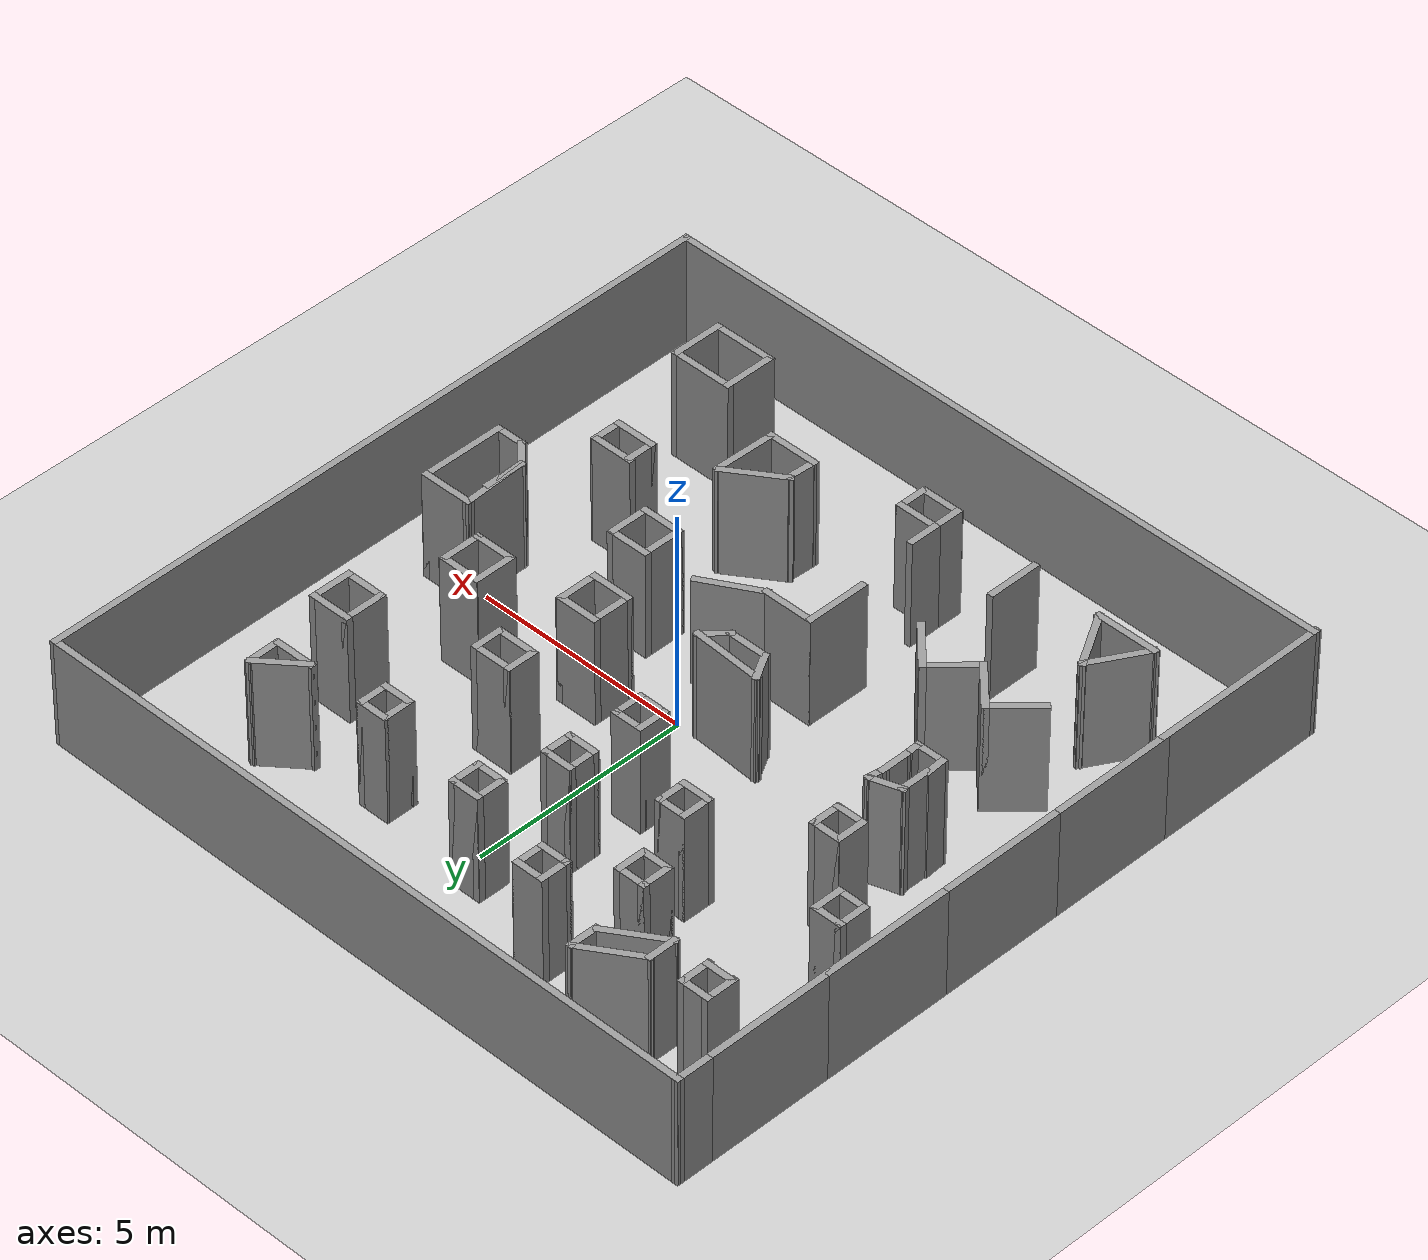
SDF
<sdf version="1.7">
 <world name="default">
  <light name="sun" type="directional">
   <pose>0 0 10 0 -0 0</pose>
   <diffuse>0.8 0.8 0.8 1</diffuse>
   <specular>0.2 0.2 0.2 1</specular>
   <attenuation>
    <range>1000</range>
    <constant>0.9</constant>
    <linear>0.01</linear>
    <quadratic>0.001</quadratic>
   </attenuation>
   <direction>-0.5 0.1 -0.9</direction>
   <spot><inner_angle>0</inner_angle><outer_angle>0</outer_angle><falloff>0</falloff></spot>
  </light>
  <model name="ground_plane">
   <static>1</static>
   <link name="link">
    <collision name="collision">
     <geometry><plane><normal>0 0 1</normal><size>100 100</size></plane></geometry>
     <surface>
      <contact><collide_bitmask>65535</collide_bitmask></contact>
      <friction><ode><mu>100</mu><mu2>50</mu2></ode></friction>
     </surface>
    </collision>
    <visual name="visual">
     <cast_shadows>0</cast_shadows>
     <geometry><plane><normal>0 0 1</normal><size>100 100</size></plane></geometry>
     <material>
      <script><uri>file://media/materials/scripts/gazebo.material</uri><name>Gazebo/Grey</name></script>
     </material>
    </visual>
   </link>
  </model>
  <gravity>0 0 -9.8</gravity>
  <magnetic_field>6e-06 2.3e-05 -4.2e-05</magnetic_field>
  <atmosphere type="adiabatic"/>
  <physics type="ode">
   <max_step_size>0.001</max_step_size>
   <real_time_factor>1</real_time_factor>
   <real_time_update_rate>1000</real_time_update_rate>
  </physics>
  <scene><ambient>0.4 0.4 0.4 1</ambient><background>0.7 0.7 0.7 1</background><shadows>1</shadows></scene>
  <spherical_coordinates>
   <surface_model>EARTH_WGS84</surface_model>
   <latitude_deg>0</latitude_deg>
   <longitude_deg>0</longitude_deg>
   <elevation>0</elevation>
   <heading_deg>0</heading_deg>
  </spherical_coordinates>
  <model name="mazeworld.sdf">
   <pose>-0.284514 0.153221 0 0 -0 0</pose>
   <link name="Wall_100">
    <collision name="Wall_100_Collision">
     <geometry><box><size>0.75 0.15 2.5</size></box></geometry>
     <pose>0 0 1.25 0 -0 0</pose>
    </collision>
    <visual name="Wall_100_Visual">
     <pose>0 0 1.25 0 -0 0</pose>
     <geometry><box><size>0.75 0.15 2.5</size></box></geometry>
     <material>
      <script><uri>file://media/materials/scripts/gazebo.material</uri><name>Gazebo/Grey</name></script>
      <ambient>1 1 1 1</ambient>
     </material>
     <meta><layer>0</layer></meta>
    </visual>
    <pose>-7.00412 2.84195 0 0 -0 0</pose>
   </link>
   <link name="Wall_101">
    <collision name="Wall_101_Collision">
     <geometry><box><size>0.75 0.15 2.5</size></box></geometry>
     <pose>0 0 1.25 0 -0 0</pose>
    </collision>
    <visual name="Wall_101_Visual">
     <pose>0 0 1.25 0 -0 0</pose>
     <geometry><box><size>0.75 0.15 2.5</size></box></geometry>
     <material>
      <script><uri>file://media/materials/scripts/gazebo.material</uri><name>Gazebo/Grey</name></script>
      <ambient>1 1 1 1</ambient>
     </material>
     <meta><layer>0</layer></meta>
    </visual>
    <pose>-6.70412 3.14195 0 0 -0 1.5708</pose>
   </link>
   <link name="Wall_102">
    <collision name="Wall_102_Collision">
     <geometry><box><size>0.75 0.15 2.5</size></box></geometry>
     <pose>0 0 1.25 0 -0 0</pose>
    </collision>
    <visual name="Wall_102_Visual">
     <pose>0 0 1.25 0 -0 0</pose>
     <geometry><box><size>0.75 0.15 2.5</size></box></geometry>
     <material>
      <script><uri>file://media/materials/scripts/gazebo.material</uri><name>Gazebo/Grey</name></script>
      <ambient>1 1 1 1</ambient>
     </material>
     <meta><layer>0</layer></meta>
    </visual>
    <pose>-7.00412 3.44195 0 0 -0 3.14159</pose>
   </link>
   <link name="Wall_106">
    <collision name="Wall_106_Collision">
     <geometry><box><size>0.75 0.15 2.5</size></box></geometry>
     <pose>0 0 1.25 0 -0 0</pose>
    </collision>
    <visual name="Wall_106_Visual">
     <pose>0 0 1.25 0 -0 0</pose>
     <geometry><box><size>0.75 0.15 2.5</size></box></geometry>
     <material>
      <script><uri>file://media/materials/scripts/gazebo.material</uri><name>Gazebo/Grey</name></script>
      <ambient>1 1 1 1</ambient>
     </material>
     <meta><layer>0</layer></meta>
    </visual>
    <pose>-0.487553 5.32416 0 0 -0 -1.5708</pose>
   </link>
   <link name="Wall_107">
    <collision name="Wall_107_Collision">
     <geometry><box><size>0.75 0.15 2.5</size></box></geometry>
     <pose>0 0 1.25 0 -0 0</pose>
    </collision>
    <visual name="Wall_107_Visual">
     <pose>0 0 1.25 0 -0 0</pose>
     <geometry><box><size>0.75 0.15 2.5</size></box></geometry>
     <material>
      <script><uri>file://media/materials/scripts/gazebo.material</uri><name>Gazebo/Grey</name></script>
      <ambient>1 1 1 1</ambient>
     </material>
     <meta><layer>0</layer></meta>
    </visual>
    <pose>-0.187553 5.02416 0 0 -0 0</pose>
   </link>
   <link name="Wall_108">
    <collision name="Wall_108_Collision">
     <geometry><box><size>0.75 0.15 2.5</size></box></geometry>
     <pose>0 0 1.25 0 -0 0</pose>
    </collision>
    <visual name="Wall_108_Visual">
     <pose>0 0 1.25 0 -0 0</pose>
     <geometry><box><size>0.75 0.15 2.5</size></box></geometry>
     <material>
      <script><uri>file://media/materials/scripts/gazebo.material</uri><name>Gazebo/Grey</name></script>
      <ambient>1 1 1 1</ambient>
     </material>
     <meta><layer>0</layer></meta>
    </visual>
    <pose>0.112447 5.32416 0 0 -0 1.5708</pose>
   </link>
   <link name="Wall_109">
    <collision name="Wall_109_Collision">
     <geometry><box><size>0.75 0.15 2.5</size></box></geometry>
     <pose>0 0 1.25 0 -0 0</pose>
    </collision>
    <visual name="Wall_109_Visual">
     <pose>0 0 1.25 0 -0 0</pose>
     <geometry><box><size>0.75 0.15 2.5</size></box></geometry>
     <material>
      <script><uri>file://media/materials/scripts/gazebo.material</uri><name>Gazebo/Grey</name></script>
      <ambient>1 1 1 1</ambient>
     </material>
     <meta><layer>0</layer></meta>
    </visual>
    <pose>-0.187553 5.62416 0 0 -0 3.14159</pose>
   </link>
   <link name="Wall_115">
    <collision name="Wall_115_Collision">
     <geometry><box><size>0.75 0.15 2.5</size></box></geometry>
     <pose>0 0 1.25 0 -0 0</pose>
    </collision>
    <visual name="Wall_115_Visual">
     <pose>0 0 1.25 0 -0 0</pose>
     <geometry><box><size>0.75 0.15 2.5</size></box></geometry>
     <material>
      <script><uri>file://media/materials/scripts/gazebo.material</uri><name>Gazebo/Grey</name></script>
      <ambient>1 1 1 1</ambient>
     </material>
     <meta><layer>0</layer></meta>
    </visual>
    <pose>-3.12317 3.39304 0 0 -0 0</pose>
   </link>
   <link name="Wall_116">
    <collision name="Wall_116_Collision">
     <geometry><box><size>0.75 0.15 2.5</size></box></geometry>
     <pose>0 0 1.25 0 -0 0</pose>
    </collision>
    <visual name="Wall_116_Visual">
     <pose>0 0 1.25 0 -0 0</pose>
     <geometry><box><size>0.75 0.15 2.5</size></box></geometry>
     <material>
      <script><uri>file://media/materials/scripts/gazebo.material</uri><name>Gazebo/Grey</name></script>
      <ambient>1 1 1 1</ambient>
     </material>
     <meta><layer>0</layer></meta>
    </visual>
    <pose>-2.82317 3.09304 0 0 -0 -1.5708</pose>
   </link>
   <link name="Wall_117">
    <collision name="Wall_117_Collision">
     <geometry><box><size>0.75 0.15 2.5</size></box></geometry>
     <pose>0 0 1.25 0 -0 0</pose>
    </collision>
    <visual name="Wall_117_Visual">
     <pose>0 0 1.25 0 -0 0</pose>
     <geometry><box><size>0.75 0.15 2.5</size></box></geometry>
     <material>
      <script><uri>file://media/materials/scripts/gazebo.material</uri><name>Gazebo/Grey</name></script>
      <ambient>1 1 1 1</ambient>
     </material>
     <meta><layer>0</layer></meta>
    </visual>
    <pose>-3.12317 2.79304 0 0 -0 3.14159</pose>
   </link>
   <link name="Wall_118">
    <collision name="Wall_118_Collision">
     <geometry><box><size>0.75 0.15 2.5</size></box></geometry>
     <pose>0 0 1.25 0 -0 0</pose>
    </collision>
    <visual name="Wall_118_Visual">
     <pose>0 0 1.25 0 -0 0</pose>
     <geometry><box><size>0.75 0.15 2.5</size></box></geometry>
     <material>
      <script><uri>file://media/materials/scripts/gazebo.material</uri><name>Gazebo/Grey</name></script>
      <ambient>1 1 1 1</ambient>
     </material>
     <meta><layer>0</layer></meta>
    </visual>
    <pose>-3.42317 3.09304 0 0 -0 1.5708</pose>
   </link>
   <link name="Wall_120">
    <collision name="Wall_120_Collision">
     <geometry><box><size>0.75 0.15 2.5</size></box></geometry>
     <pose>0 0 1.25 0 -0 0</pose>
    </collision>
    <visual name="Wall_120_Visual">
     <pose>0 0 1.25 0 -0 0</pose>
     <geometry><box><size>0.75 0.15 2.5</size></box></geometry>
     <material>
      <script><uri>file://media/materials/scripts/gazebo.material</uri><name>Gazebo/Grey</name></script>
      <ambient>1 1 1 1</ambient>
     </material>
     <meta><layer>0</layer></meta>
    </visual>
    <pose>-1.0967 3.63685 0 0 -0 -1.5708</pose>
   </link>
   <link name="Wall_121">
    <collision name="Wall_121_Collision">
     <geometry><box><size>0.75 0.15 2.5</size></box></geometry>
     <pose>0 0 1.25 0 -0 0</pose>
    </collision>
    <visual name="Wall_121_Visual">
     <pose>0 0 1.25 0 -0 0</pose>
     <geometry><box><size>0.75 0.15 2.5</size></box></geometry>
     <material>
      <script><uri>file://media/materials/scripts/gazebo.material</uri><name>Gazebo/Grey</name></script>
      <ambient>1 1 1 1</ambient>
     </material>
     <meta><layer>0</layer></meta>
    </visual>
    <pose>-0.796699 3.33685 0 0 -0 0</pose>
   </link>
   <link name="Wall_122">
    <collision name="Wall_122_Collision">
     <geometry><box><size>0.75 0.15 2.5</size></box></geometry>
     <pose>0 0 1.25 0 -0 0</pose>
    </collision>
    <visual name="Wall_122_Visual">
     <pose>0 0 1.25 0 -0 0</pose>
     <geometry><box><size>0.75 0.15 2.5</size></box></geometry>
     <material>
      <script><uri>file://media/materials/scripts/gazebo.material</uri><name>Gazebo/Grey</name></script>
      <ambient>1 1 1 1</ambient>
     </material>
     <meta><layer>0</layer></meta>
    </visual>
    <pose>-0.496698 3.63685 0 0 -0 1.5708</pose>
   </link>
   <link name="Wall_123">
    <collision name="Wall_123_Collision">
     <geometry><box><size>0.75 0.15 2.5</size></box></geometry>
     <pose>0 0 1.25 0 -0 0</pose>
    </collision>
    <visual name="Wall_123_Visual">
     <pose>0 0 1.25 0 -0 0</pose>
     <geometry><box><size>0.75 0.15 2.5</size></box></geometry>
     <material>
      <script><uri>file://media/materials/scripts/gazebo.material</uri><name>Gazebo/Grey</name></script>
      <ambient>1 1 1 1</ambient>
     </material>
     <meta><layer>0</layer></meta>
    </visual>
    <pose>-0.796699 3.93685 0 0 -0 3.14159</pose>
   </link>
   <link name="Wall_125">
    <collision name="Wall_125_Collision">
     <geometry><box><size>0.75 0.15 2.5</size></box></geometry>
     <pose>0 0 1.25 0 -0 0</pose>
    </collision>
    <visual name="Wall_125_Visual">
     <pose>0 0 1.25 0 -0 0</pose>
     <geometry><box><size>0.75 0.15 2.5</size></box></geometry>
     <material>
      <script><uri>file://media/materials/scripts/gazebo.material</uri><name>Gazebo/Grey</name></script>
      <ambient>1 1 1 1</ambient>
     </material>
     <meta><layer>0</layer></meta>
    </visual>
    <pose>-5.77172 1.5986 0 0 -0 -1.5708</pose>
   </link>
   <link name="Wall_126">
    <collision name="Wall_126_Collision">
     <geometry><box><size>0.75 0.15 2.5</size></box></geometry>
     <pose>0 0 1.25 0 -0 0</pose>
    </collision>
    <visual name="Wall_126_Visual">
     <pose>0 0 1.25 0 -0 0</pose>
     <geometry><box><size>0.75 0.15 2.5</size></box></geometry>
     <material>
      <script><uri>file://media/materials/scripts/gazebo.material</uri><name>Gazebo/Grey</name></script>
      <ambient>1 1 1 1</ambient>
     </material>
     <meta><layer>0</layer></meta>
    </visual>
    <pose>-5.47172 1.2986 0 0 -0 0</pose>
   </link>
   <link name="Wall_127">
    <collision name="Wall_127_Collision">
     <geometry><box><size>0.75 0.15 2.5</size></box></geometry>
     <pose>0 0 1.25 0 -0 0</pose>
    </collision>
    <visual name="Wall_127_Visual">
     <pose>0 0 1.25 0 -0 0</pose>
     <geometry><box><size>0.75 0.15 2.5</size></box></geometry>
     <material>
      <script><uri>file://media/materials/scripts/gazebo.material</uri><name>Gazebo/Grey</name></script>
      <ambient>1 1 1 1</ambient>
     </material>
     <meta><layer>0</layer></meta>
    </visual>
    <pose>-5.17172 1.5986 0 0 -0 1.5708</pose>
   </link>
   <link name="Wall_128">
    <collision name="Wall_128_Collision">
     <geometry><box><size>0.75 0.15 2.5</size></box></geometry>
     <pose>0 0 1.25 0 -0 0</pose>
    </collision>
    <visual name="Wall_128_Visual">
     <pose>0 0 1.25 0 -0 0</pose>
     <geometry><box><size>0.75 0.15 2.5</size></box></geometry>
     <material>
      <script><uri>file://media/materials/scripts/gazebo.material</uri><name>Gazebo/Grey</name></script>
      <ambient>1 1 1 1</ambient>
     </material>
     <meta><layer>0</layer></meta>
    </visual>
    <pose>-5.47172 1.8986 0 0 -0 3.14159</pose>
   </link>
   <link name="Wall_131">
    <collision name="Wall_131_Collision">
     <geometry><box><size>1 0.15 2.5</size></box></geometry>
     <pose>0 0 1.25 0 -0 0</pose>
    </collision>
    <visual name="Wall_131_Visual">
     <pose>0 0 1.25 0 -0 0</pose>
     <geometry><box><size>1 0.15 2.5</size></box></geometry>
     <material>
      <script><uri>file://media/materials/scripts/gazebo.material</uri><name>Gazebo/Grey</name></script>
      <ambient>1 1 1 1</ambient>
     </material>
     <meta><layer>0</layer></meta>
    </visual>
    <pose>-8.01051 7.72393 0 0 -0 1.5708</pose>
   </link>
   <link name="Wall_132">
    <collision name="Wall_132_Collision">
     <geometry><box><size>16.0032 0.15 2.5</size></box></geometry>
     <pose>0 0 1.25 0 -0 0</pose>
    </collision>
    <visual name="Wall_132_Visual">
     <pose>0 0 1.25 0 -0 0</pose>
     <geometry><box><size>16.0032 0.15 2.5</size></box></geometry>
     <material>
      <script><uri>file://media/materials/scripts/gazebo.material</uri><name>Gazebo/Grey</name></script>
      <ambient>1 1 1 1</ambient>
     </material>
     <meta><layer>0</layer></meta>
    </visual>
    <pose>-0.083946 8.13102 0 0 -0 -0.00226</pose>
   </link>
   <link name="Wall_135">
    <collision name="Wall_135_Collision">
     <geometry><box><size>0.75 0.15 2.5</size></box></geometry>
     <pose>0 0 1.25 0 -0 0</pose>
    </collision>
    <visual name="Wall_135_Visual">
     <pose>0 0 1.25 0 -0 0</pose>
     <geometry><box><size>0.75 0.15 2.5</size></box></geometry>
     <material>
      <script><uri>file://media/materials/scripts/gazebo.material</uri><name>Gazebo/Grey</name></script>
      <ambient>1 1 1 1</ambient>
     </material>
     <meta><layer>0</layer></meta>
    </visual>
    <pose>2.18363 5.04113 0 0 -0 -1.5708</pose>
   </link>
   <link name="Wall_136">
    <collision name="Wall_136_Collision">
     <geometry><box><size>0.75 0.15 2.5</size></box></geometry>
     <pose>0 0 1.25 0 -0 0</pose>
    </collision>
    <visual name="Wall_136_Visual">
     <pose>0 0 1.25 0 -0 0</pose>
     <geometry><box><size>0.75 0.15 2.5</size></box></geometry>
     <material>
      <script><uri>file://media/materials/scripts/gazebo.material</uri><name>Gazebo/Grey</name></script>
      <ambient>1 1 1 1</ambient>
     </material>
     <meta><layer>0</layer></meta>
    </visual>
    <pose>2.48363 4.74113 0 0 -0 0</pose>
   </link>
   <link name="Wall_137">
    <collision name="Wall_137_Collision">
     <geometry><box><size>0.75 0.15 2.5</size></box></geometry>
     <pose>0 0 1.25 0 -0 0</pose>
    </collision>
    <visual name="Wall_137_Visual">
     <pose>0 0 1.25 0 -0 0</pose>
     <geometry><box><size>0.75 0.15 2.5</size></box></geometry>
     <material>
      <script><uri>file://media/materials/scripts/gazebo.material</uri><name>Gazebo/Grey</name></script>
      <ambient>1 1 1 1</ambient>
     </material>
     <meta><layer>0</layer></meta>
    </visual>
    <pose>2.78363 5.04113 0 0 -0 1.5708</pose>
   </link>
   <link name="Wall_138">
    <collision name="Wall_138_Collision">
     <geometry><box><size>0.75 0.15 2.5</size></box></geometry>
     <pose>0 0 1.25 0 -0 0</pose>
    </collision>
    <visual name="Wall_138_Visual">
     <pose>0 0 1.25 0 -0 0</pose>
     <geometry><box><size>0.75 0.15 2.5</size></box></geometry>
     <material>
      <script><uri>file://media/materials/scripts/gazebo.material</uri><name>Gazebo/Grey</name></script>
      <ambient>1 1 1 1</ambient>
     </material>
     <meta><layer>0</layer></meta>
    </visual>
    <pose>2.48363 5.34113 0 0 -0 3.14159</pose>
   </link>
   <link name="Wall_140">
    <collision name="Wall_140_Collision">
     <geometry><box><size>1.23478 0.15 2.5</size></box></geometry>
     <pose>0 0 1.25 0 -0 0</pose>
    </collision>
    <visual name="Wall_140_Visual">
     <pose>0 0 1.25 0 -0 0</pose>
     <geometry><box><size>1.23478 0.15 2.5</size></box></geometry>
     <material>
      <script><uri>file://media/materials/scripts/gazebo.material</uri><name>Gazebo/Grey</name></script>
      <ambient>1 1 1 1</ambient>
     </material>
     <meta><layer>0</layer></meta>
    </visual>
    <pose>4.59414 5.64718 0 0 -0 -2.45294</pose>
   </link>
   <link name="Wall_141">
    <collision name="Wall_141_Collision">
     <geometry><box><size>1 0.15 2.5</size></box></geometry>
     <pose>0 0 1.25 0 -0 0</pose>
    </collision>
    <visual name="Wall_141_Visual">
     <pose>0 0 1.25 0 -0 0</pose>
     <geometry><box><size>1 0.15 2.5</size></box></geometry>
     <material>
      <script><uri>file://media/materials/scripts/gazebo.material</uri><name>Gazebo/Grey</name></script>
      <ambient>1 1 1 1</ambient>
     </material>
     <meta><layer>0</layer></meta>
    </visual>
    <pose>4.57206 5.30249 0 0 -0 0</pose>
   </link>
   <link name="Wall_142">
    <collision name="Wall_142_Collision">
     <geometry><box><size>0.839555 0.15 2.5</size></box></geometry>
     <pose>0 0 1.25 0 -0 0</pose>
    </collision>
    <visual name="Wall_142_Visual">
     <pose>0 0 1.25 0 -0 0</pose>
     <geometry><box><size>0.839555 0.15 2.5</size></box></geometry>
     <material>
      <script><uri>file://media/materials/scripts/gazebo.material</uri><name>Gazebo/Grey</name></script>
      <ambient>1 1 1 1</ambient>
     </material>
     <meta><layer>0</layer></meta>
    </visual>
    <pose>5.01914 5.64718 0 0 -0 1.58883</pose>
   </link>
   <link name="Wall_144">
    <collision name="Wall_144_Collision">
     <geometry><box><size>0.75 0.15 2.5</size></box></geometry>
     <pose>0 0 1.25 0 -0 0</pose>
    </collision>
    <visual name="Wall_144_Visual">
     <pose>0 0 1.25 0 -0 0</pose>
     <geometry><box><size>0.75 0.15 2.5</size></box></geometry>
     <material>
      <script><uri>file://media/materials/scripts/gazebo.material</uri><name>Gazebo/Grey</name></script>
      <ambient>1 1 1 1</ambient>
     </material>
     <meta><layer>0</layer></meta>
    </visual>
    <pose>1.56119 2.55135 0 0 -0 -1.5708</pose>
   </link>
   <link name="Wall_145">
    <collision name="Wall_145_Collision">
     <geometry><box><size>1 0.15 2.5</size></box></geometry>
     <pose>0 0 1.25 0 -0 0</pose>
    </collision>
    <visual name="Wall_145_Visual">
     <pose>0 0 1.25 0 -0 0</pose>
     <geometry><box><size>1 0.15 2.5</size></box></geometry>
     <material>
      <script><uri>file://media/materials/scripts/gazebo.material</uri><name>Gazebo/Grey</name></script>
      <ambient>1 1 1 1</ambient>
     </material>
     <meta><layer>0</layer></meta>
    </visual>
    <pose>1.98619 2.25135 0 0 -0 0</pose>
   </link>
   <link name="Wall_146">
    <collision name="Wall_146_Collision">
     <geometry><box><size>0.75 0.15 2.5</size></box></geometry>
     <pose>0 0 1.25 0 -0 0</pose>
    </collision>
    <visual name="Wall_146_Visual">
     <pose>0 0 1.25 0 -0 0</pose>
     <geometry><box><size>0.75 0.15 2.5</size></box></geometry>
     <material>
      <script><uri>file://media/materials/scripts/gazebo.material</uri><name>Gazebo/Grey</name></script>
      <ambient>1 1 1 1</ambient>
     </material>
     <meta><layer>0</layer></meta>
    </visual>
    <pose>2.41119 2.55135 0 0 -0 1.5708</pose>
   </link>
   <link name="Wall_147">
    <collision name="Wall_147_Collision">
     <geometry><box><size>1 0.15 2.5</size></box></geometry>
     <pose>0 0 1.25 0 -0 0</pose>
    </collision>
    <visual name="Wall_147_Visual">
     <pose>0 0 1.25 0 -0 0</pose>
     <geometry><box><size>1 0.15 2.5</size></box></geometry>
     <material>
      <script><uri>file://media/materials/scripts/gazebo.material</uri><name>Gazebo/Grey</name></script>
      <ambient>1 1 1 1</ambient>
     </material>
     <meta><layer>0</layer></meta>
    </visual>
    <pose>1.98619 2.85135 0 0 -0 3.14159</pose>
   </link>
   <link name="Wall_149">
    <collision name="Wall_149_Collision">
     <geometry><box><size>0.75 0.15 2.5</size></box></geometry>
     <pose>0 0 1.25 0 -0 0</pose>
    </collision>
    <visual name="Wall_149_Visual">
     <pose>0 0 1.25 0 -0 0</pose>
     <geometry><box><size>0.75 0.15 2.5</size></box></geometry>
     <material>
      <script><uri>file://media/materials/scripts/gazebo.material</uri><name>Gazebo/Grey</name></script>
      <ambient>1 1 1 1</ambient>
     </material>
     <meta><layer>0</layer></meta>
    </visual>
    <pose>-1.23981 2.01378 0 0 -0 -1.5708</pose>
   </link>
   <link name="Wall_150">
    <collision name="Wall_150_Collision">
     <geometry><box><size>0.75 0.15 2.5</size></box></geometry>
     <pose>0 0 1.25 0 -0 0</pose>
    </collision>
    <visual name="Wall_150_Visual">
     <pose>0 0 1.25 0 -0 0</pose>
     <geometry><box><size>0.75 0.15 2.5</size></box></geometry>
     <material>
      <script><uri>file://media/materials/scripts/gazebo.material</uri><name>Gazebo/Grey</name></script>
      <ambient>1 1 1 1</ambient>
     </material>
     <meta><layer>0</layer></meta>
    </visual>
    <pose>-0.939811 1.71378 0 0 -0 0</pose>
   </link>
   <link name="Wall_151">
    <collision name="Wall_151_Collision">
     <geometry><box><size>0.75 0.15 2.5</size></box></geometry>
     <pose>0 0 1.25 0 -0 0</pose>
    </collision>
    <visual name="Wall_151_Visual">
     <pose>0 0 1.25 0 -0 0</pose>
     <geometry><box><size>0.75 0.15 2.5</size></box></geometry>
     <material>
      <script><uri>file://media/materials/scripts/gazebo.material</uri><name>Gazebo/Grey</name></script>
      <ambient>1 1 1 1</ambient>
     </material>
     <meta><layer>0</layer></meta>
    </visual>
    <pose>-0.639811 2.01378 0 0 -0 1.5708</pose>
   </link>
   <link name="Wall_152">
    <collision name="Wall_152_Collision">
     <geometry><box><size>0.75 0.15 2.5</size></box></geometry>
     <pose>0 0 1.25 0 -0 0</pose>
    </collision>
    <visual name="Wall_152_Visual">
     <pose>0 0 1.25 0 -0 0</pose>
     <geometry><box><size>0.75 0.15 2.5</size></box></geometry>
     <material>
      <script><uri>file://media/materials/scripts/gazebo.material</uri><name>Gazebo/Grey</name></script>
      <ambient>1 1 1 1</ambient>
     </material>
     <meta><layer>0</layer></meta>
    </visual>
    <pose>-0.939811 2.31379 0 0 -0 3.14159</pose>
   </link>
   <link name="Wall_154">
    <collision name="Wall_154_Collision">
     <geometry><box><size>0.778293 0.15 2.5</size></box></geometry>
     <pose>0 0 1.25 0 -0 0</pose>
    </collision>
    <visual name="Wall_154_Visual">
     <pose>0 0 1.25 0 -0 0</pose>
     <geometry><box><size>0.778293 0.15 2.5</size></box></geometry>
     <material>
      <script><uri>file://media/materials/scripts/gazebo.material</uri><name>Gazebo/Grey</name></script>
      <ambient>1 1 1 1</ambient>
     </material>
     <meta><layer>0</layer></meta>
    </visual>
    <pose>-5.6535 -0.150621 0 0 -0 -1.5708</pose>
   </link>
   <link name="Wall_155">
    <collision name="Wall_155_Collision">
     <geometry><box><size>0.546971 0.15 2.5</size></box></geometry>
     <pose>0 0 1.25 0 -0 0</pose>
    </collision>
    <visual name="Wall_155_Visual">
     <pose>0 0 1.25 0 -0 0</pose>
     <geometry><box><size>0.546971 0.15 2.5</size></box></geometry>
     <material>
      <script><uri>file://media/materials/scripts/gazebo.material</uri><name>Gazebo/Grey</name></script>
      <ambient>1 1 1 1</ambient>
     </material>
     <meta><layer>0</layer></meta>
    </visual>
    <pose>-5.66772 -0.662753 0 0 -0 -1.49979</pose>
   </link>
   <link name="Wall_156">
    <collision name="Wall_156_Collision">
     <geometry><box><size>0.75 0.15 2.5</size></box></geometry>
     <pose>0 0 1.25 0 -0 0</pose>
    </collision>
    <visual name="Wall_156_Visual">
     <pose>0 0 1.25 0 -0 0</pose>
     <geometry><box><size>0.75 0.15 2.5</size></box></geometry>
     <material>
      <script><uri>file://media/materials/scripts/gazebo.material</uri><name>Gazebo/Grey</name></script>
      <ambient>1 1 1 1</ambient>
     </material>
     <meta><layer>0</layer></meta>
    </visual>
    <pose>-5.35363 -0.860739 0 0 -0 0</pose>
   </link>
   <link name="Wall_157">
    <collision name="Wall_157_Collision">
     <geometry><box><size>0.450537 0.15 2.5</size></box></geometry>
     <pose>0 0 1.25 0 -0 0</pose>
    </collision>
    <visual name="Wall_157_Visual">
     <pose>0 0 1.25 0 -0 0</pose>
     <geometry><box><size>0.450537 0.15 2.5</size></box></geometry>
     <material>
      <script><uri>file://media/materials/scripts/gazebo.material</uri><name>Gazebo/Grey</name></script>
      <ambient>1 1 1 1</ambient>
     </material>
     <meta><layer>0</layer></meta>
    </visual>
    <pose>-5.06261 -0.710739 0 0 -0 1.63056</pose>
   </link>
   <link name="Wall_158">
    <collision name="Wall_158_Collision">
     <geometry><box><size>0.75 0.15 2.5</size></box></geometry>
     <pose>0 0 1.25 0 -0 0</pose>
    </collision>
    <visual name="Wall_158_Visual">
     <pose>0 0 1.25 0 -0 0</pose>
     <geometry><box><size>0.75 0.15 2.5</size></box></geometry>
     <material>
      <script><uri>file://media/materials/scripts/gazebo.material</uri><name>Gazebo/Grey</name></script>
      <ambient>1 1 1 1</ambient>
     </material>
     <meta><layer>0</layer></meta>
    </visual>
    <pose>-5.07158 -0.232446 0 0 -0 1.5708</pose>
   </link>
   <link name="Wall_159">
    <collision name="Wall_159_Collision">
     <geometry><box><size>0.480559 0.15 2.5</size></box></geometry>
     <pose>0 0 1.25 0 -0 0</pose>
    </collision>
    <visual name="Wall_159_Visual">
     <pose>0 0 1.25 0 -0 0</pose>
     <geometry><box><size>0.480559 0.15 2.5</size></box></geometry>
     <material>
      <script><uri>file://media/materials/scripts/gazebo.material</uri><name>Gazebo/Grey</name></script>
      <ambient>1 1 1 1</ambient>
     </material>
     <meta><layer>0</layer></meta>
    </visual>
    <pose>-5.04846 0.203407 0 0 -0 1.43086</pose>
   </link>
   <link name="Wall_160">
    <collision name="Wall_160_Collision">
     <geometry><box><size>0.810467 0.15 2.5</size></box></geometry>
     <pose>0 0 1.25 0 -0 0</pose>
    </collision>
    <visual name="Wall_160_Visual">
     <pose>0 0 1.25 0 -0 0</pose>
     <geometry><box><size>0.810467 0.15 2.5</size></box></geometry>
     <material>
      <script><uri>file://media/materials/scripts/gazebo.material</uri><name>Gazebo/Grey</name></script>
      <ambient>1 1 1 1</ambient>
     </material>
     <meta><layer>0</layer></meta>
    </visual>
    <pose>-5.36771 0.265539 0 0 -0 -2.82754</pose>
   </link>
   <link name="Wall_162">
    <collision name="Wall_162_Collision">
     <geometry><box><size>0.75 0.15 2.5</size></box></geometry>
     <pose>0 0 1.25 0 -0 0</pose>
    </collision>
    <visual name="Wall_162_Visual">
     <pose>0 0 1.25 0 -0 0</pose>
     <geometry><box><size>0.75 0.15 2.5</size></box></geometry>
     <material>
      <script><uri>file://media/materials/scripts/gazebo.material</uri><name>Gazebo/Grey</name></script>
      <ambient>1 1 1 1</ambient>
     </material>
     <meta><layer>0</layer></meta>
    </visual>
    <pose>-1.59908 -0.379212 0 0 -0 -1.0472</pose>
   </link>
   <link name="Wall_163">
    <collision name="Wall_163_Collision">
     <geometry><box><size>1 0.15 2.5</size></box></geometry>
     <pose>0 0 1.25 0 -0 0</pose>
    </collision>
    <visual name="Wall_163_Visual">
     <pose>0 0 1.25 0 -0 0</pose>
     <geometry><box><size>1 0.15 2.5</size></box></geometry>
     <material>
      <script><uri>file://media/materials/scripts/gazebo.material</uri><name>Gazebo/Grey</name></script>
      <ambient>1 1 1 1</ambient>
     </material>
     <meta><layer>0</layer></meta>
    </visual>
    <pose>-1.02408 -0.639019 0 0 -0 0</pose>
   </link>
   <link name="Wall_164">
    <collision name="Wall_164_Collision">
     <geometry><box><size>0.75 0.15 2.5</size></box></geometry>
     <pose>0 0 1.25 0 -0 0</pose>
    </collision>
    <visual name="Wall_164_Visual">
     <pose>0 0 1.25 0 -0 0</pose>
     <geometry><box><size>0.75 0.15 2.5</size></box></geometry>
     <material>
      <script><uri>file://media/materials/scripts/gazebo.material</uri><name>Gazebo/Grey</name></script>
      <ambient>1 1 1 1</ambient>
     </material>
     <meta><layer>0</layer></meta>
    </visual>
    <pose>-0.386951 -0.426887 0 0 -0 0.785398</pose>
   </link>
   <link name="Wall_165">
    <collision name="Wall_165_Collision">
     <geometry><box><size>1.72715 0.15 2.5</size></box></geometry>
     <pose>0 0 1.25 0 -0 0</pose>
    </collision>
    <visual name="Wall_165_Visual">
     <pose>0 0 1.25 0 -0 0</pose>
     <geometry><box><size>1.72715 0.15 2.5</size></box></geometry>
     <material>
      <script><uri>file://media/materials/scripts/gazebo.material</uri><name>Gazebo/Grey</name></script>
      <ambient>1 1 1 1</ambient>
     </material>
     <meta><layer>0</layer></meta>
    </visual>
    <pose>-0.961951 -0.16708 0 0 -0 3.0811</pose>
   </link>
   <link name="Wall_167">
    <collision name="Wall_167_Collision">
     <geometry><box><size>1 0.15 2.5</size></box></geometry>
     <pose>0 0 1.25 0 -0 0</pose>
    </collision>
    <visual name="Wall_167_Visual">
     <pose>0 0 1.25 0 -0 0</pose>
     <geometry><box><size>1 0.15 2.5</size></box></geometry>
     <material>
      <script><uri>file://media/materials/scripts/gazebo.material</uri><name>Gazebo/Grey</name></script>
      <ambient>1 1 1 1</ambient>
     </material>
     <meta><layer>0</layer></meta>
    </visual>
    <pose>1.41972 0.417555 0 0 -0 -1.5708</pose>
   </link>
   <link name="Wall_168">
    <collision name="Wall_168_Collision">
     <geometry><box><size>1 0.15 2.5</size></box></geometry>
     <pose>0 0 1.25 0 -0 0</pose>
    </collision>
    <visual name="Wall_168_Visual">
     <pose>0 0 1.25 0 -0 0</pose>
     <geometry><box><size>1 0.15 2.5</size></box></geometry>
     <material>
      <script><uri>file://media/materials/scripts/gazebo.material</uri><name>Gazebo/Grey</name></script>
      <ambient>1 1 1 1</ambient>
     </material>
     <meta><layer>0</layer></meta>
    </visual>
    <pose>1.84472 -0.007445 0 0 -0 0</pose>
   </link>
   <link name="Wall_169">
    <collision name="Wall_169_Collision">
     <geometry><box><size>1 0.15 2.5</size></box></geometry>
     <pose>0 0 1.25 0 -0 0</pose>
    </collision>
    <visual name="Wall_169_Visual">
     <pose>0 0 1.25 0 -0 0</pose>
     <geometry><box><size>1 0.15 2.5</size></box></geometry>
     <material>
      <script><uri>file://media/materials/scripts/gazebo.material</uri><name>Gazebo/Grey</name></script>
      <ambient>1 1 1 1</ambient>
     </material>
     <meta><layer>0</layer></meta>
    </visual>
    <pose>2.26972 0.417555 0 0 -0 1.5708</pose>
   </link>
   <link name="Wall_170">
    <collision name="Wall_170_Collision">
     <geometry><box><size>1 0.15 2.5</size></box></geometry>
     <pose>0 0 1.25 0 -0 0</pose>
    </collision>
    <visual name="Wall_170_Visual">
     <pose>0 0 1.25 0 -0 0</pose>
     <geometry><box><size>1 0.15 2.5</size></box></geometry>
     <material>
      <script><uri>file://media/materials/scripts/gazebo.material</uri><name>Gazebo/Grey</name></script>
      <ambient>1 1 1 1</ambient>
     </material>
     <meta><layer>0</layer></meta>
    </visual>
    <pose>1.84472 0.842555 0 0 -0 3.14159</pose>
   </link>
   <link name="Wall_172">
    <collision name="Wall_172_Collision">
     <geometry><box><size>1 0.15 2.5</size></box></geometry>
     <pose>0 0 1.25 0 -0 0</pose>
    </collision>
    <visual name="Wall_172_Visual">
     <pose>0 0 1.25 0 -0 0</pose>
     <geometry><box><size>1 0.15 2.5</size></box></geometry>
     <material>
      <script><uri>file://media/materials/scripts/gazebo.material</uri><name>Gazebo/Grey</name></script>
      <ambient>1 1 1 1</ambient>
     </material>
     <meta><layer>0</layer></meta>
    </visual>
    <pose>2.07046 -1.53466 0 0 -0 -1.5708</pose>
   </link>
   <link name="Wall_173">
    <collision name="Wall_173_Collision">
     <geometry><box><size>1 0.15 2.5</size></box></geometry>
     <pose>0 0 1.25 0 -0 0</pose>
    </collision>
    <visual name="Wall_173_Visual">
     <pose>0 0 1.25 0 -0 0</pose>
     <geometry><box><size>1 0.15 2.5</size></box></geometry>
     <material>
      <script><uri>file://media/materials/scripts/gazebo.material</uri><name>Gazebo/Grey</name></script>
      <ambient>1 1 1 1</ambient>
     </material>
     <meta><layer>0</layer></meta>
    </visual>
    <pose>2.49546 -1.95966 0 0 -0 0</pose>
   </link>
   <link name="Wall_174">
    <collision name="Wall_174_Collision">
     <geometry><box><size>1 0.15 2.5</size></box></geometry>
     <pose>0 0 1.25 0 -0 0</pose>
    </collision>
    <visual name="Wall_174_Visual">
     <pose>0 0 1.25 0 -0 0</pose>
     <geometry><box><size>1 0.15 2.5</size></box></geometry>
     <material>
      <script><uri>file://media/materials/scripts/gazebo.material</uri><name>Gazebo/Grey</name></script>
      <ambient>1 1 1 1</ambient>
     </material>
     <meta><layer>0</layer></meta>
    </visual>
    <pose>2.92046 -1.53466 0 0 -0 1.5708</pose>
   </link>
   <link name="Wall_175">
    <collision name="Wall_175_Collision">
     <geometry><box><size>1 0.15 2.5</size></box></geometry>
     <pose>0 0 1.25 0 -0 0</pose>
    </collision>
    <visual name="Wall_175_Visual">
     <pose>0 0 1.25 0 -0 0</pose>
     <geometry><box><size>1 0.15 2.5</size></box></geometry>
     <material>
      <script><uri>file://media/materials/scripts/gazebo.material</uri><name>Gazebo/Grey</name></script>
      <ambient>1 1 1 1</ambient>
     </material>
     <meta><layer>0</layer></meta>
    </visual>
    <pose>2.49546 -1.10966 0 0 -0 3.14159</pose>
   </link>
   <link name="Wall_177">
    <collision name="Wall_177_Collision">
     <geometry><box><size>1 0.15 2.5</size></box></geometry>
     <pose>0 0 1.25 0 -0 0</pose>
    </collision>
    <visual name="Wall_177_Visual">
     <pose>0 0 1.25 0 -0 0</pose>
     <geometry><box><size>1 0.15 2.5</size></box></geometry>
     <material>
      <script><uri>file://media/materials/scripts/gazebo.material</uri><name>Gazebo/Grey</name></script>
      <ambient>1 1 1 1</ambient>
     </material>
     <meta><layer>0</layer></meta>
    </visual>
    <pose>3.71145 1.15317 0 0 -0 -1.5708</pose>
   </link>
   <link name="Wall_178">
    <collision name="Wall_178_Collision">
     <geometry><box><size>1 0.15 2.5</size></box></geometry>
     <pose>0 0 1.25 0 -0 0</pose>
    </collision>
    <visual name="Wall_178_Visual">
     <pose>0 0 1.25 0 -0 0</pose>
     <geometry><box><size>1 0.15 2.5</size></box></geometry>
     <material>
      <script><uri>file://media/materials/scripts/gazebo.material</uri><name>Gazebo/Grey</name></script>
      <ambient>1 1 1 1</ambient>
     </material>
     <meta><layer>0</layer></meta>
    </visual>
    <pose>4.13645 0.72817 0 0 -0 0</pose>
   </link>
   <link name="Wall_179">
    <collision name="Wall_179_Collision">
     <geometry><box><size>1 0.15 2.5</size></box></geometry>
     <pose>0 0 1.25 0 -0 0</pose>
    </collision>
    <visual name="Wall_179_Visual">
     <pose>0 0 1.25 0 -0 0</pose>
     <geometry><box><size>1 0.15 2.5</size></box></geometry>
     <material>
      <script><uri>file://media/materials/scripts/gazebo.material</uri><name>Gazebo/Grey</name></script>
      <ambient>1 1 1 1</ambient>
     </material>
     <meta><layer>0</layer></meta>
    </visual>
    <pose>4.56145 1.15317 0 0 -0 1.5708</pose>
   </link>
   <link name="Wall_180">
    <collision name="Wall_180_Collision">
     <geometry><box><size>1 0.15 2.5</size></box></geometry>
     <pose>0 0 1.25 0 -0 0</pose>
    </collision>
    <visual name="Wall_180_Visual">
     <pose>0 0 1.25 0 -0 0</pose>
     <geometry><box><size>1 0.15 2.5</size></box></geometry>
     <material>
      <script><uri>file://media/materials/scripts/gazebo.material</uri><name>Gazebo/Grey</name></script>
      <ambient>1 1 1 1</ambient>
     </material>
     <meta><layer>0</layer></meta>
    </visual>
    <pose>4.13645 1.57817 0 0 -0 3.14159</pose>
   </link>
   <link name="Wall_182">
    <collision name="Wall_182_Collision">
     <geometry><box><size>1.25 0.15 2.5</size></box></geometry>
     <pose>0 0 1.25 0 -0 0</pose>
    </collision>
    <visual name="Wall_182_Visual">
     <pose>0 0 1.25 0 -0 0</pose>
     <geometry><box><size>1.25 0.15 2.5</size></box></geometry>
     <material>
      <script><uri>file://media/materials/scripts/gazebo.material</uri><name>Gazebo/Grey</name></script>
      <ambient>1 1 1 1</ambient>
     </material>
     <meta><layer>0</layer></meta>
    </visual>
    <pose>-5.57582 -2.84271 0 0 -0 0.785398</pose>
   </link>
   <link name="Wall_183">
    <collision name="Wall_183_Collision">
     <geometry><box><size>1.25 0.15 2.5</size></box></geometry>
     <pose>0 0 1.25 0 -0 0</pose>
    </collision>
    <visual name="Wall_183_Visual">
     <pose>0 0 1.25 0 -0 0</pose>
     <geometry><box><size>1.25 0.15 2.5</size></box></geometry>
     <material>
      <script><uri>file://media/materials/scripts/gazebo.material</uri><name>Gazebo/Grey</name></script>
      <ambient>1 1 1 1</ambient>
     </material>
     <meta><layer>0</layer></meta>
    </visual>
    <pose>-4.798 -2.84271 0 0 -0 -0.785398</pose>
   </link>
   <link name="Wall_185">
    <collision name="Wall_185_Collision">
     <geometry><box><size>1.25 0.15 2.5</size></box></geometry>
     <pose>0 0 1.25 0 -0 0</pose>
    </collision>
    <visual name="Wall_185_Visual">
     <pose>0 0 1.25 0 -0 0</pose>
     <geometry><box><size>1.25 0.15 2.5</size></box></geometry>
     <material>
      <script><uri>file://media/materials/scripts/gazebo.material</uri><name>Gazebo/Grey</name></script>
      <ambient>1 1 1 1</ambient>
     </material>
     <meta><layer>0</layer></meta>
    </visual>
    <pose>-4.02018 -2.84271 0 0 -0 0.785398</pose>
   </link>
   <link name="Wall_186">
    <collision name="Wall_186_Collision">
     <geometry><box><size>1.25 0.15 2.5</size></box></geometry>
     <pose>0 0 1.25 0 -0 0</pose>
    </collision>
    <visual name="Wall_186_Visual">
     <pose>0 0 1.25 0 -0 0</pose>
     <geometry><box><size>1.25 0.15 2.5</size></box></geometry>
     <material>
      <script><uri>file://media/materials/scripts/gazebo.material</uri><name>Gazebo/Grey</name></script>
      <ambient>1 1 1 1</ambient>
     </material>
     <meta><layer>0</layer></meta>
    </visual>
    <pose>-3.24236 -2.84271 0 0 -0 -0.785398</pose>
   </link>
   <link name="Wall_188">
    <collision name="Wall_188_Collision">
     <geometry><box><size>1.5 0.15 2.5</size></box></geometry>
     <pose>0 0 1.25 0 -0 0</pose>
    </collision>
    <visual name="Wall_188_Visual">
     <pose>0 0 1.25 0 -0 0</pose>
     <geometry><box><size>1.5 0.15 2.5</size></box></geometry>
     <material>
      <script><uri>file://media/materials/scripts/gazebo.material</uri><name>Gazebo/Grey</name></script>
      <ambient>1 1 1 1</ambient>
     </material>
     <meta><layer>0</layer></meta>
    </visual>
    <pose>-1.35298 -2.58492 0 0 -0 1.5708</pose>
   </link>
   <link name="Wall_189">
    <collision name="Wall_189_Collision">
     <geometry><box><size>1.25 0.15 2.5</size></box></geometry>
     <pose>0 0 1.25 0 -0 0</pose>
    </collision>
    <visual name="Wall_189_Visual">
     <pose>0 0 1.25 0 -0 0</pose>
     <geometry><box><size>1.25 0.15 2.5</size></box></geometry>
     <material>
      <script><uri>file://media/materials/scripts/gazebo.material</uri><name>Gazebo/Grey</name></script>
      <ambient>1 1 1 1</ambient>
     </material>
     <meta><layer>0</layer></meta>
    </visual>
    <pose>-0.802983 -1.90992 0 0 -0 0</pose>
   </link>
   <link name="Wall_190">
    <collision name="Wall_190_Collision">
     <geometry><box><size>1.5 0.15 2.5</size></box></geometry>
     <pose>0 0 1.25 0 -0 0</pose>
    </collision>
    <visual name="Wall_190_Visual">
     <pose>0 0 1.25 0 -0 0</pose>
     <geometry><box><size>1.5 0.15 2.5</size></box></geometry>
     <material>
      <script><uri>file://media/materials/scripts/gazebo.material</uri><name>Gazebo/Grey</name></script>
      <ambient>1 1 1 1</ambient>
     </material>
     <meta><layer>0</layer></meta>
    </visual>
    <pose>0.331584 -1.57242 0 0 -0 0.523599</pose>
   </link>
   <link name="Wall_192">
    <collision name="Wall_192_Collision">
     <geometry><box><size>0.75 0.15 2.5</size></box></geometry>
     <pose>0 0 1.25 0 -0 0</pose>
    </collision>
    <visual name="Wall_192_Visual">
     <pose>0 0 1.25 0 -0 0</pose>
     <geometry><box><size>0.75 0.15 2.5</size></box></geometry>
     <material>
      <script><uri>file://media/materials/scripts/gazebo.material</uri><name>Gazebo/Grey</name></script>
      <ambient>1 1 1 1</ambient>
     </material>
     <meta><layer>0</layer></meta>
    </visual>
    <pose>4.16413 -3.05064 0 0 -0 -1.5708</pose>
   </link>
   <link name="Wall_193">
    <collision name="Wall_193_Collision">
     <geometry><box><size>1 0.15 2.5</size></box></geometry>
     <pose>0 0 1.25 0 -0 0</pose>
    </collision>
    <visual name="Wall_193_Visual">
     <pose>0 0 1.25 0 -0 0</pose>
     <geometry><box><size>1 0.15 2.5</size></box></geometry>
     <material>
      <script><uri>file://media/materials/scripts/gazebo.material</uri><name>Gazebo/Grey</name></script>
      <ambient>1 1 1 1</ambient>
     </material>
     <meta><layer>0</layer></meta>
    </visual>
    <pose>4.58913 -3.35064 0 0 -0 0</pose>
   </link>
   <link name="Wall_194">
    <collision name="Wall_194_Collision">
     <geometry><box><size>0.75 0.15 2.5</size></box></geometry>
     <pose>0 0 1.25 0 -0 0</pose>
    </collision>
    <visual name="Wall_194_Visual">
     <pose>0 0 1.25 0 -0 0</pose>
     <geometry><box><size>0.75 0.15 2.5</size></box></geometry>
     <material>
      <script><uri>file://media/materials/scripts/gazebo.material</uri><name>Gazebo/Grey</name></script>
      <ambient>1 1 1 1</ambient>
     </material>
     <meta><layer>0</layer></meta>
    </visual>
    <pose>5.01413 -3.05064 0 0 -0 1.5708</pose>
   </link>
   <link name="Wall_197">
    <collision name="Wall_197_Collision">
     <geometry><box><size>1 0.15 2.5</size></box></geometry>
     <pose>0 0 1.25 0 -0 0</pose>
    </collision>
    <visual name="Wall_197_Visual">
     <pose>0 0 1.25 0 -0 0</pose>
     <geometry><box><size>1 0.15 2.5</size></box></geometry>
     <material>
      <script><uri>file://media/materials/scripts/gazebo.material</uri><name>Gazebo/Grey</name></script>
      <ambient>1 1 1 1</ambient>
     </material>
     <meta><layer>0</layer></meta>
    </visual>
    <pose>4.55331 -2.75064 0 0 -0 0</pose>
   </link>
   <link name="Wall_199">
    <collision name="Wall_199_Collision">
     <geometry><box><size>1 0.15 2.5</size></box></geometry>
     <pose>0 0 1.25 0 -0 0</pose>
    </collision>
    <visual name="Wall_199_Visual">
     <pose>0 0 1.25 0 -0 0</pose>
     <geometry><box><size>1 0.15 2.5</size></box></geometry>
     <material>
      <script><uri>file://media/materials/scripts/gazebo.material</uri><name>Gazebo/Grey</name></script>
      <ambient>1 1 1 1</ambient>
     </material>
     <meta><layer>0</layer></meta>
    </visual>
    <pose>4.62757 3.53703 0 0 -0 -1.5708</pose>
   </link>
   <link name="Wall_200">
    <collision name="Wall_200_Collision">
     <geometry><box><size>1 0.15 2.5</size></box></geometry>
     <pose>0 0 1.25 0 -0 0</pose>
    </collision>
    <visual name="Wall_200_Visual">
     <pose>0 0 1.25 0 -0 0</pose>
     <geometry><box><size>1 0.15 2.5</size></box></geometry>
     <material>
      <script><uri>file://media/materials/scripts/gazebo.material</uri><name>Gazebo/Grey</name></script>
      <ambient>1 1 1 1</ambient>
     </material>
     <meta><layer>0</layer></meta>
    </visual>
    <pose>5.05257 3.11203 0 0 -0 0</pose>
   </link>
   <link name="Wall_201">
    <collision name="Wall_201_Collision">
     <geometry><box><size>1 0.15 2.5</size></box></geometry>
     <pose>0 0 1.25 0 -0 0</pose>
    </collision>
    <visual name="Wall_201_Visual">
     <pose>0 0 1.25 0 -0 0</pose>
     <geometry><box><size>1 0.15 2.5</size></box></geometry>
     <material>
      <script><uri>file://media/materials/scripts/gazebo.material</uri><name>Gazebo/Grey</name></script>
      <ambient>1 1 1 1</ambient>
     </material>
     <meta><layer>0</layer></meta>
    </visual>
    <pose>5.47757 3.53703 0 0 -0 1.5708</pose>
   </link>
   <link name="Wall_202">
    <collision name="Wall_202_Collision">
     <geometry><box><size>1 0.15 2.5</size></box></geometry>
     <pose>0 0 1.25 0 -0 0</pose>
    </collision>
    <visual name="Wall_202_Visual">
     <pose>0 0 1.25 0 -0 0</pose>
     <geometry><box><size>1 0.15 2.5</size></box></geometry>
     <material>
      <script><uri>file://media/materials/scripts/gazebo.material</uri><name>Gazebo/Grey</name></script>
      <ambient>1 1 1 1</ambient>
     </material>
     <meta><layer>0</layer></meta>
    </visual>
    <pose>5.05257 3.96203 0 0 -0 3.14159</pose>
   </link>
   <link name="Wall_204">
    <collision name="Wall_204_Collision">
     <geometry><box><size>1.5 0.15 2.5</size></box></geometry>
     <pose>0 0 1.25 0 -0 0</pose>
    </collision>
    <visual name="Wall_204_Visual">
     <pose>0 0 1.25 0 -0 0</pose>
     <geometry><box><size>1.5 0.15 2.5</size></box></geometry>
     <material>
      <script><uri>file://media/materials/scripts/gazebo.material</uri><name>Gazebo/Grey</name></script>
      <ambient>1 1 1 1</ambient>
     </material>
     <meta><layer>0</layer></meta>
    </visual>
    <pose>-5.9805 -5.10528 0 0 -0 1.0472</pose>
   </link>
   <link name="Wall_205">
    <collision name="Wall_205_Collision">
     <geometry><box><size>1.5 0.15 2.5</size></box></geometry>
     <pose>0 0 1.25 0 -0 0</pose>
    </collision>
    <visual name="Wall_205_Visual">
     <pose>0 0 1.25 0 -0 0</pose>
     <geometry><box><size>1.5 0.15 2.5</size></box></geometry>
     <material>
      <script><uri>file://media/materials/scripts/gazebo.material</uri><name>Gazebo/Grey</name></script>
      <ambient>1 1 1 1</ambient>
     </material>
     <meta><layer>0</layer></meta>
    </visual>
    <pose>-5.30551 -5.10528 0 0 -0 -1.0472</pose>
   </link>
   <link name="Wall_206">
    <collision name="Wall_206_Collision">
     <geometry><box><size>1.5 0.15 2.5</size></box></geometry>
     <pose>0 0 1.25 0 -0 0</pose>
    </collision>
    <visual name="Wall_206_Visual">
     <pose>0 0 1.25 0 -0 0</pose>
     <geometry><box><size>1.5 0.15 2.5</size></box></geometry>
     <material>
      <script><uri>file://media/materials/scripts/gazebo.material</uri><name>Gazebo/Grey</name></script>
      <ambient>1 1 1 1</ambient>
     </material>
     <meta><layer>0</layer></meta>
    </visual>
    <pose>-5.643 -5.68984 0 0 -0 3.14159</pose>
   </link>
   <link name="Wall_209">
    <collision name="Wall_209_Collision">
     <geometry><box><size>1.25 0.15 2.5</size></box></geometry>
     <pose>0 0 1.25 0 -0 0</pose>
    </collision>
    <visual name="Wall_209_Visual">
     <pose>0 0 1.25 0 -0 0</pose>
     <geometry><box><size>1.25 0.15 2.5</size></box></geometry>
     <material>
      <script><uri>file://media/materials/scripts/gazebo.material</uri><name>Gazebo/Grey</name></script>
      <ambient>1 1 1 1</ambient>
     </material>
     <meta><layer>0</layer></meta>
    </visual>
    <pose>-3.19455 -5.31099 0 0 -0 1.5708</pose>
   </link>
   <link name="Wall_212">
    <collision name="Wall_212_Collision">
     <geometry><box><size>16.3828 0.15 2.5</size></box></geometry>
     <pose>0 0 1.25 0 -0 0</pose>
    </collision>
    <visual name="Wall_212_Visual">
     <pose>0 0 1.25 0 -0 0</pose>
     <geometry><box><size>16.3828 0.15 2.5</size></box></geometry>
     <material>
      <script><uri>file://media/materials/scripts/gazebo.material</uri><name>Gazebo/Grey</name></script>
      <ambient>1 1 1 1</ambient>
     </material>
     <meta><layer>0</layer></meta>
    </visual>
    <pose>7.94426 -0.003003 0 0 -0 -1.56269</pose>
   </link>
   <link name="Wall_215">
    <collision name="Wall_215_Collision">
     <geometry><box><size>0.75 0.15 2.5</size></box></geometry>
     <pose>0 0 1.25 0 -0 0</pose>
    </collision>
    <visual name="Wall_215_Visual">
     <pose>0 0 1.25 0 -0 0</pose>
     <geometry><box><size>0.75 0.15 2.5</size></box></geometry>
     <material>
      <script><uri>file://media/materials/scripts/gazebo.material</uri><name>Gazebo/Grey</name></script>
      <ambient>1 1 1 1</ambient>
     </material>
     <meta><layer>0</layer></meta>
    </visual>
    <pose>-1.15999 -5.07272 0 0 -0 -1.5708</pose>
   </link>
   <link name="Wall_216">
    <collision name="Wall_216_Collision">
     <geometry><box><size>1 0.15 2.5</size></box></geometry>
     <pose>0 0 1.25 0 -0 0</pose>
    </collision>
    <visual name="Wall_216_Visual">
     <pose>0 0 1.25 0 -0 0</pose>
     <geometry><box><size>1 0.15 2.5</size></box></geometry>
     <material>
      <script><uri>file://media/materials/scripts/gazebo.material</uri><name>Gazebo/Grey</name></script>
      <ambient>1 1 1 1</ambient>
     </material>
     <meta><layer>0</layer></meta>
    </visual>
    <pose>-0.734989 -5.37272 0 0 -0 0</pose>
   </link>
   <link name="Wall_217">
    <collision name="Wall_217_Collision">
     <geometry><box><size>0.75 0.15 2.5</size></box></geometry>
     <pose>0 0 1.25 0 -0 0</pose>
    </collision>
    <visual name="Wall_217_Visual">
     <pose>0 0 1.25 0 -0 0</pose>
     <geometry><box><size>0.75 0.15 2.5</size></box></geometry>
     <material>
      <script><uri>file://media/materials/scripts/gazebo.material</uri><name>Gazebo/Grey</name></script>
      <ambient>1 1 1 1</ambient>
     </material>
     <meta><layer>0</layer></meta>
    </visual>
    <pose>-0.309989 -5.67272 0 0 -0 -1.5708</pose>
   </link>
   <link name="Wall_218">
    <collision name="Wall_218_Collision">
     <geometry><box><size>1 0.15 2.5</size></box></geometry>
     <pose>0 0 1.25 0 -0 0</pose>
    </collision>
    <visual name="Wall_218_Visual">
     <pose>0 0 1.25 0 -0 0</pose>
     <geometry><box><size>1 0.15 2.5</size></box></geometry>
     <material>
      <script><uri>file://media/materials/scripts/gazebo.material</uri><name>Gazebo/Grey</name></script>
      <ambient>1 1 1 1</ambient>
     </material>
     <meta><layer>0</layer></meta>
    </visual>
    <pose>-0.734989 -5.97272 0 0 -0 3.14159</pose>
   </link>
   <link name="Wall_219">
    <collision name="Wall_219_Collision">
     <geometry><box><size>0.75 0.15 2.5</size></box></geometry>
     <pose>0 0 1.25 0 -0 0</pose>
    </collision>
    <visual name="Wall_219_Visual">
     <pose>0 0 1.25 0 -0 0</pose>
     <geometry><box><size>0.75 0.15 2.5</size></box></geometry>
     <material>
      <script><uri>file://media/materials/scripts/gazebo.material</uri><name>Gazebo/Grey</name></script>
      <ambient>1 1 1 1</ambient>
     </material>
     <meta><layer>0</layer></meta>
    </visual>
    <pose>-1.15999 -5.67272 0 0 -0 1.5708</pose>
   </link>
   <link name="Wall_223">
    <collision name="Wall_223_Collision">
     <geometry><box><size>0.770679 0.15 2.5</size></box></geometry>
     <pose>0 0 1.25 0 -0 0</pose>
    </collision>
    <visual name="Wall_223_Visual">
     <pose>0 0 1.25 0 -0 0</pose>
     <geometry><box><size>0.770679 0.15 2.5</size></box></geometry>
     <material>
      <script><uri>file://media/materials/scripts/gazebo.material</uri><name>Gazebo/Grey</name></script>
      <ambient>1 1 1 1</ambient>
     </material>
     <meta><layer>0</layer></meta>
    </visual>
    <pose>1.68817 -4.79593 0 0 -0 -1.62855</pose>
   </link>
   <link name="Wall_224">
    <collision name="Wall_224_Collision">
     <geometry><box><size>1.25 0.15 2.5</size></box></geometry>
     <pose>0 0 1.25 0 -0 0</pose>
    </collision>
    <visual name="Wall_224_Visual">
     <pose>0 0 1.25 0 -0 0</pose>
     <geometry><box><size>1.25 0.15 2.5</size></box></geometry>
     <material>
      <script><uri>file://media/materials/scripts/gazebo.material</uri><name>Gazebo/Grey</name></script>
      <ambient>1 1 1 1</ambient>
     </material>
     <meta><layer>0</layer></meta>
    </visual>
    <pose>2.22026 -5.10575 0 0 -0 0</pose>
   </link>
   <link name="Wall_225">
    <collision name="Wall_225_Collision">
     <geometry><box><size>1.51964 0.15 2.5</size></box></geometry>
     <pose>0 0 1.25 0 -0 0</pose>
    </collision>
    <visual name="Wall_225_Visual">
     <pose>0 0 1.25 0 -0 0</pose>
     <geometry><box><size>1.51964 0.15 2.5</size></box></geometry>
     <material>
      <script><uri>file://media/materials/scripts/gazebo.material</uri><name>Gazebo/Grey</name></script>
      <ambient>1 1 1 1</ambient>
     </material>
     <meta><layer>0</layer></meta>
    </visual>
    <pose>2.78817 -4.42093 0 0 -0 1.54465</pose>
   </link>
   <link name="Wall_226">
    <collision name="Wall_226_Collision">
     <geometry><box><size>1.48135 0.15 2.5</size></box></geometry>
     <pose>0 0 1.25 0 -0 0</pose>
    </collision>
    <visual name="Wall_226_Visual">
     <pose>0 0 1.25 0 -0 0</pose>
     <geometry><box><size>1.48135 0.15 2.5</size></box></geometry>
     <material>
      <script><uri>file://media/materials/scripts/gazebo.material</uri><name>Gazebo/Grey</name></script>
      <ambient>1 1 1 1</ambient>
     </material>
     <meta><layer>0</layer></meta>
    </visual>
    <pose>2.22026 -4.11111 0 0 -0 -2.54317</pose>
   </link>
   <link name="Wall_228">
    <collision name="Wall_228_Collision">
     <geometry><box><size>1.25 0.15 2.5</size></box></geometry>
     <pose>0 0 1.25 0 -0 0</pose>
    </collision>
    <visual name="Wall_228_Visual">
     <pose>0 0 1.25 0 -0 0</pose>
     <geometry><box><size>1.25 0.15 2.5</size></box></geometry>
     <material>
      <script><uri>file://media/materials/scripts/gazebo.material</uri><name>Gazebo/Grey</name></script>
      <ambient>1 1 1 1</ambient>
     </material>
     <meta><layer>0</layer></meta>
    </visual>
    <pose>4.3572 -6.11089 0 0 -0 -1.5708</pose>
   </link>
   <link name="Wall_229">
    <collision name="Wall_229_Collision">
     <geometry><box><size>1.5 0.15 2.5</size></box></geometry>
     <pose>0 0 1.25 0 -0 0</pose>
    </collision>
    <visual name="Wall_229_Visual">
     <pose>0 0 1.25 0 -0 0</pose>
     <geometry><box><size>1.5 0.15 2.5</size></box></geometry>
     <material>
      <script><uri>file://media/materials/scripts/gazebo.material</uri><name>Gazebo/Grey</name></script>
      <ambient>1 1 1 1</ambient>
     </material>
     <meta><layer>0</layer></meta>
    </visual>
    <pose>5.0322 -6.66089 0 0 -0 0</pose>
   </link>
   <link name="Wall_230">
    <collision name="Wall_230_Collision">
     <geometry><box><size>1.25 0.15 2.5</size></box></geometry>
     <pose>0 0 1.25 0 -0 0</pose>
    </collision>
    <visual name="Wall_230_Visual">
     <pose>0 0 1.25 0 -0 0</pose>
     <geometry><box><size>1.25 0.15 2.5</size></box></geometry>
     <material>
      <script><uri>file://media/materials/scripts/gazebo.material</uri><name>Gazebo/Grey</name></script>
      <ambient>1 1 1 1</ambient>
     </material>
     <meta><layer>0</layer></meta>
    </visual>
    <pose>5.7072 -6.11089 0 0 -0 1.5708</pose>
   </link>
   <link name="Wall_231">
    <collision name="Wall_231_Collision">
     <geometry><box><size>1.5 0.15 2.5</size></box></geometry>
     <pose>0 0 1.25 0 -0 0</pose>
    </collision>
    <visual name="Wall_231_Visual">
     <pose>0 0 1.25 0 -0 0</pose>
     <geometry><box><size>1.5 0.15 2.5</size></box></geometry>
     <material>
      <script><uri>file://media/materials/scripts/gazebo.material</uri><name>Gazebo/Grey</name></script>
      <ambient>1 1 1 1</ambient>
     </material>
     <meta><layer>0</layer></meta>
    </visual>
    <pose>5.0322 -5.56089 0 0 -0 3.14159</pose>
   </link>
   <link name="Wall_233">
    <collision name="Wall_233_Collision">
     <geometry><box><size>1 0.15 2.5</size></box></geometry>
     <pose>0 0 1.25 0 -0 0</pose>
    </collision>
    <visual name="Wall_233_Visual">
     <pose>0 0 1.25 0 -0 0</pose>
     <geometry><box><size>1 0.15 2.5</size></box></geometry>
     <material>
      <script><uri>file://media/materials/scripts/gazebo.material</uri><name>Gazebo/Grey</name></script>
      <ambient>1 1 1 1</ambient>
     </material>
     <meta><layer>0</layer></meta>
    </visual>
    <pose>5.46781 -0.826954 0 0 -0 -1.5708</pose>
   </link>
   <link name="Wall_234">
    <collision name="Wall_234_Collision">
     <geometry><box><size>0.75 0.15 2.5</size></box></geometry>
     <pose>0 0 1.25 0 -0 0</pose>
    </collision>
    <visual name="Wall_234_Visual">
     <pose>0 0 1.25 0 -0 0</pose>
     <geometry><box><size>0.75 0.15 2.5</size></box></geometry>
     <material>
      <script><uri>file://media/materials/scripts/gazebo.material</uri><name>Gazebo/Grey</name></script>
      <ambient>1 1 1 1</ambient>
     </material>
     <meta><layer>0</layer></meta>
    </visual>
    <pose>5.67994 -1.46409 0 0 -0 -0.785398</pose>
   </link>
   <link name="Wall_235">
    <collision name="Wall_235_Collision">
     <geometry><box><size>0.75 0.15 2.5</size></box></geometry>
     <pose>0 0 1.25 0 -0 0</pose>
    </collision>
    <visual name="Wall_235_Visual">
     <pose>0 0 1.25 0 -0 0</pose>
     <geometry><box><size>0.75 0.15 2.5</size></box></geometry>
     <material>
      <script><uri>file://media/materials/scripts/gazebo.material</uri><name>Gazebo/Grey</name></script>
      <ambient>1 1 1 1</ambient>
     </material>
     <meta><layer>0</layer></meta>
    </visual>
    <pose>6.19207 -1.67622 0 0 -0 0</pose>
   </link>
   <link name="Wall_236">
    <collision name="Wall_236_Collision">
     <geometry><box><size>2 0.15 2.5</size></box></geometry>
     <pose>0 0 1.25 0 -0 0</pose>
    </collision>
    <visual name="Wall_236_Visual">
     <pose>0 0 1.25 0 -0 0</pose>
     <geometry><box><size>2 0.15 2.5</size></box></geometry>
     <material>
      <script><uri>file://media/materials/scripts/gazebo.material</uri><name>Gazebo/Grey</name></script>
      <ambient>1 1 1 1</ambient>
     </material>
     <meta><layer>0</layer></meta>
    </visual>
    <pose>6.49207 -0.751218 0 0 -0 1.5708</pose>
   </link>
   <link name="Wall_242">
    <collision name="Wall_242_Collision">
     <geometry><box><size>1.25 0.15 2.5</size></box></geometry>
     <pose>0 0 1.25 0 -0 0</pose>
    </collision>
    <visual name="Wall_242_Visual">
     <pose>0 0 1.25 0 -0 0</pose>
     <geometry><box><size>1.25 0.15 2.5</size></box></geometry>
     <material>
      <script><uri>file://media/materials/scripts/gazebo.material</uri><name>Gazebo/Grey</name></script>
      <ambient>1 1 1 1</ambient>
     </material>
     <meta><layer>0</layer></meta>
    </visual>
    <pose>5.94207 0.173782 0 0 -0 3.14159</pose>
   </link>
   <link name="Wall_243">
    <collision name="Wall_243_Collision">
     <geometry><box><size>1.57775 0.15 2.5</size></box></geometry>
     <pose>0 0 1.25 0 -0 0</pose>
    </collision>
    <visual name="Wall_243_Visual">
     <pose>0 0 1.25 0 -0 0</pose>
     <geometry><box><size>1.57775 0.15 2.5</size></box></geometry>
     <material>
      <script><uri>file://media/materials/scripts/gazebo.material</uri><name>Gazebo/Grey</name></script>
      <ambient>1 1 1 1</ambient>
     </material>
     <meta><layer>0</layer></meta>
    </visual>
    <pose>5.42994 -0.539086 0 0 -0 -1.51773</pose>
   </link>
   <link name="Wall_44">
    <collision name="Wall_44_Collision">
     <geometry><box><size>3 0.15 2.5</size></box></geometry>
     <pose>0 0 1.25 0 -0 0</pose>
    </collision>
    <visual name="Wall_44_Visual">
     <pose>0 0 1.25 0 -0 0</pose>
     <geometry><box><size>3 0.15 2.5</size></box></geometry>
     <material>
      <script><uri>file://media/materials/scripts/gazebo.material</uri><name>Gazebo/Grey</name></script>
      <ambient>1 1 1 1</ambient>
     </material>
     <meta><layer>0</layer></meta>
    </visual>
    <pose>-8.01051 0.173933 0 0 -0 -1.5708</pose>
   </link>
   <link name="Wall_46">
    <collision name="Wall_46_Collision">
     <geometry><box><size>3 0.15 2.5</size></box></geometry>
     <pose>0 0 1.25 0 -0 0</pose>
    </collision>
    <visual name="Wall_46_Visual">
     <pose>0 0 1.25 0 -0 0</pose>
     <geometry><box><size>3 0.15 2.5</size></box></geometry>
     <material>
      <script><uri>file://media/materials/scripts/gazebo.material</uri><name>Gazebo/Grey</name></script>
      <ambient>1 1 1 1</ambient>
     </material>
     <meta><layer>0</layer></meta>
    </visual>
    <pose>-8.01051 -2.67607 0 0 -0 -1.5708</pose>
   </link>
   <link name="Wall_48">
    <collision name="Wall_48_Collision">
     <geometry><box><size>4.19804 0.15 2.5</size></box></geometry>
     <pose>0 0 1.25 0 -0 0</pose>
    </collision>
    <visual name="Wall_48_Visual">
     <pose>0 0 1.25 0 -0 0</pose>
     <geometry><box><size>4.19804 0.15 2.5</size></box></geometry>
     <material>
      <script><uri>file://media/materials/scripts/gazebo.material</uri><name>Gazebo/Grey</name></script>
      <ambient>1 1 1 1</ambient>
     </material>
     <meta><layer>0</layer></meta>
    </visual>
    <pose>-8.01051 -6.12509 0 0 -0 -1.5708</pose>
   </link>
   <link name="Wall_51">
    <collision name="Wall_51_Collision">
     <geometry><box><size>3 0.15 2.5</size></box></geometry>
     <pose>0 0 1.25 0 -0 0</pose>
    </collision>
    <visual name="Wall_51_Visual">
     <pose>0 0 1.25 0 -0 0</pose>
     <geometry><box><size>3 0.15 2.5</size></box></geometry>
     <material>
      <script><uri>file://media/materials/scripts/gazebo.material</uri><name>Gazebo/Grey</name></script>
      <ambient>1 1 1 1</ambient>
     </material>
     <meta><layer>0</layer></meta>
    </visual>
    <pose>-8.01051 3.02393 0 0 -0 1.5708</pose>
   </link>
   <link name="Wall_52">
    <collision name="Wall_52_Collision">
     <geometry><box><size>3 0.15 2.5</size></box></geometry>
     <pose>0 0 1.25 0 -0 0</pose>
    </collision>
    <visual name="Wall_52_Visual">
     <pose>0 0 1.25 0 -0 0</pose>
     <geometry><box><size>3 0.15 2.5</size></box></geometry>
     <material>
      <script><uri>file://media/materials/scripts/gazebo.material</uri><name>Gazebo/Grey</name></script>
      <ambient>1 1 1 1</ambient>
     </material>
     <meta><layer>0</layer></meta>
    </visual>
    <pose>-8.01051 5.87393 0 0 -0 1.5708</pose>
   </link>
   <link name="Wall_66">
    <collision name="Wall_66_Collision">
     <geometry><box><size>16.1348 0.15 2.5</size></box></geometry>
     <pose>0 0 1.25 0 -0 0</pose>
    </collision>
    <visual name="Wall_66_Visual">
     <pose>0 0 1.25 0 -0 0</pose>
     <geometry><box><size>16.1348 0.15 2.5</size></box></geometry>
     <material>
      <script><uri>file://media/materials/scripts/gazebo.material</uri><name>Gazebo/Grey</name></script>
      <ambient>1 1 1 1</ambient>
     </material>
     <meta><layer>0</layer></meta>
    </visual>
    <pose>-0.018131 -8.11271 0 0 -0 3.14079</pose>
   </link>
   <link name="Wall_79">
    <collision name="Wall_79_Collision">
     <geometry><box><size>0.778293 0.15 2.5</size></box></geometry>
     <pose>0 0 1.25 0 -0 0</pose>
    </collision>
    <visual name="Wall_79_Visual">
     <pose>0 0 1.25 0 -0 0</pose>
     <geometry><box><size>0.778293 0.15 2.5</size></box></geometry>
     <material>
      <script><uri>file://media/materials/scripts/gazebo.material</uri><name>Gazebo/Grey</name></script>
      <ambient>1 1 1 1</ambient>
     </material>
     <meta><layer>0</layer></meta>
    </visual>
    <pose>-6.96849 6.06287 0 0 -0 -1.5708</pose>
   </link>
   <link name="Wall_80">
    <collision name="Wall_80_Collision">
     <geometry><box><size>0.75 0.15 2.5</size></box></geometry>
     <pose>0 0 1.25 0 -0 0</pose>
    </collision>
    <visual name="Wall_80_Visual">
     <pose>0 0 1.25 0 -0 0</pose>
     <geometry><box><size>0.75 0.15 2.5</size></box></geometry>
     <material>
      <script><uri>file://media/materials/scripts/gazebo.material</uri><name>Gazebo/Grey</name></script>
      <ambient>1 1 1 1</ambient>
     </material>
     <meta><layer>0</layer></meta>
    </visual>
    <pose>-6.66848 5.77701 0 0 -0 0</pose>
   </link>
   <link name="Wall_81">
    <collision name="Wall_81_Collision">
     <geometry><box><size>0.778293 0.15 2.5</size></box></geometry>
     <pose>0 0 1.25 0 -0 0</pose>
    </collision>
    <visual name="Wall_81_Visual">
     <pose>0 0 1.25 0 -0 0</pose>
     <geometry><box><size>0.778293 0.15 2.5</size></box></geometry>
     <material>
      <script><uri>file://media/materials/scripts/gazebo.material</uri><name>Gazebo/Grey</name></script>
      <ambient>1 1 1 1</ambient>
     </material>
     <meta><layer>0</layer></meta>
    </visual>
    <pose>-6.36848 6.06287 0 0 -0 1.5708</pose>
   </link>
   <link name="Wall_82">
    <collision name="Wall_82_Collision">
     <geometry><box><size>0.75 0.15 2.5</size></box></geometry>
     <pose>0 0 1.25 0 -0 0</pose>
    </collision>
    <visual name="Wall_82_Visual">
     <pose>0 0 1.25 0 -0 0</pose>
     <geometry><box><size>0.75 0.15 2.5</size></box></geometry>
     <material>
      <script><uri>file://media/materials/scripts/gazebo.material</uri><name>Gazebo/Grey</name></script>
      <ambient>1 1 1 1</ambient>
     </material>
     <meta><layer>0</layer></meta>
    </visual>
    <pose>-6.66848 6.37701 0 0 -0 3.14159</pose>
   </link>
   <link name="Wall_84">
    <collision name="Wall_84_Collision">
     <geometry><box><size>0.75 0.15 2.5</size></box></geometry>
     <pose>0 0 1.25 0 -0 0</pose>
    </collision>
    <visual name="Wall_84_Visual">
     <pose>0 0 1.25 0 -0 0</pose>
     <geometry><box><size>0.75 0.15 2.5</size></box></geometry>
     <material>
      <script><uri>file://media/materials/scripts/gazebo.material</uri><name>Gazebo/Grey</name></script>
      <ambient>1 1 1 1</ambient>
     </material>
     <meta><layer>0</layer></meta>
    </visual>
    <pose>-5.54936 6.06655 0 0 -0 -1.5708</pose>
   </link>
   <link name="Wall_85">
    <collision name="Wall_85_Collision">
     <geometry><box><size>1.52511 0.15 2.5</size></box></geometry>
     <pose>0 0 1.25 0 -0 0</pose>
    </collision>
    <visual name="Wall_85_Visual">
     <pose>0 0 1.25 0 -0 0</pose>
     <geometry><box><size>1.52511 0.15 2.5</size></box></geometry>
     <material>
      <script><uri>file://media/materials/scripts/gazebo.material</uri><name>Gazebo/Grey</name></script>
      <ambient>1 1 1 1</ambient>
     </material>
     <meta><layer>0</layer></meta>
    </visual>
    <pose>-4.97073 6.13793 0 0 -0 0.570605</pose>
   </link>
   <link name="Wall_86">
    <collision name="Wall_86_Collision">
     <geometry><box><size>0.75 0.15 2.5</size></box></geometry>
     <pose>0 0 1.25 0 -0 0</pose>
    </collision>
    <visual name="Wall_86_Visual">
     <pose>0 0 1.25 0 -0 0</pose>
     <geometry><box><size>0.75 0.15 2.5</size></box></geometry>
     <material>
      <script><uri>file://media/materials/scripts/gazebo.material</uri><name>Gazebo/Grey</name></script>
      <ambient>1 1 1 1</ambient>
     </material>
     <meta><layer>0</layer></meta>
    </visual>
    <pose>-4.36381 6.80931 0 0 -0 1.5708</pose>
   </link>
   <link name="Wall_87">
    <collision name="Wall_87_Collision">
     <geometry><box><size>1.52511 0.15 2.5</size></box></geometry>
     <pose>0 0 1.25 0 -0 0</pose>
    </collision>
    <visual name="Wall_87_Visual">
     <pose>0 0 1.25 0 -0 0</pose>
     <geometry><box><size>1.52511 0.15 2.5</size></box></geometry>
     <material>
      <script><uri>file://media/materials/scripts/gazebo.material</uri><name>Gazebo/Grey</name></script>
      <ambient>1 1 1 1</ambient>
     </material>
     <meta><layer>0</layer></meta>
    </visual>
    <pose>-4.97073 6.73793 0 0 -0 -2.57099</pose>
   </link>
   <link name="Wall_89">
    <collision name="Wall_89_Collision">
     <geometry><box><size>0.75 0.15 2.5</size></box></geometry>
     <pose>0 0 1.25 0 -0 0</pose>
    </collision>
    <visual name="Wall_89_Visual">
     <pose>0 0 1.25 0 -0 0</pose>
     <geometry><box><size>0.75 0.15 2.5</size></box></geometry>
     <material>
      <script><uri>file://media/materials/scripts/gazebo.material</uri><name>Gazebo/Grey</name></script>
      <ambient>1 1 1 1</ambient>
     </material>
     <meta><layer>0</layer></meta>
    </visual>
    <pose>-4.17705 4.85172 0 0 -0 -1.5708</pose>
   </link>
   <link name="Wall_90">
    <collision name="Wall_90_Collision">
     <geometry><box><size>0.75 0.15 2.5</size></box></geometry>
     <pose>0 0 1.25 0 -0 0</pose>
    </collision>
    <visual name="Wall_90_Visual">
     <pose>0 0 1.25 0 -0 0</pose>
     <geometry><box><size>0.75 0.15 2.5</size></box></geometry>
     <material>
      <script><uri>file://media/materials/scripts/gazebo.material</uri><name>Gazebo/Grey</name></script>
      <ambient>1 1 1 1</ambient>
     </material>
     <meta><layer>0</layer></meta>
    </visual>
    <pose>-3.87705 4.55172 0 0 -0 0</pose>
   </link>
   <link name="Wall_91">
    <collision name="Wall_91_Collision">
     <geometry><box><size>0.75 0.15 2.5</size></box></geometry>
     <pose>0 0 1.25 0 -0 0</pose>
    </collision>
    <visual name="Wall_91_Visual">
     <pose>0 0 1.25 0 -0 0</pose>
     <geometry><box><size>0.75 0.15 2.5</size></box></geometry>
     <material>
      <script><uri>file://media/materials/scripts/gazebo.material</uri><name>Gazebo/Grey</name></script>
      <ambient>1 1 1 1</ambient>
     </material>
     <meta><layer>0</layer></meta>
    </visual>
    <pose>-3.57705 4.85172 0 0 -0 1.5708</pose>
   </link>
   <link name="Wall_92">
    <collision name="Wall_92_Collision">
     <geometry><box><size>0.75 0.15 2.5</size></box></geometry>
     <pose>0 0 1.25 0 -0 0</pose>
    </collision>
    <visual name="Wall_92_Visual">
     <pose>0 0 1.25 0 -0 0</pose>
     <geometry><box><size>0.75 0.15 2.5</size></box></geometry>
     <material>
      <script><uri>file://media/materials/scripts/gazebo.material</uri><name>Gazebo/Grey</name></script>
      <ambient>1 1 1 1</ambient>
     </material>
     <meta><layer>0</layer></meta>
    </visual>
    <pose>-3.87705 5.15172 0 0 -0 3.14159</pose>
   </link>
   <link name="Wall_94">
    <collision name="Wall_94_Collision">
     <geometry><box><size>0.75 0.15 2.5</size></box></geometry>
     <pose>0 0 1.25 0 -0 0</pose>
    </collision>
    <visual name="Wall_94_Visual">
     <pose>0 0 1.25 0 -0 0</pose>
     <geometry><box><size>0.75 0.15 2.5</size></box></geometry>
     <material>
      <script><uri>file://media/materials/scripts/gazebo.material</uri><name>Gazebo/Grey</name></script>
      <ambient>1 1 1 1</ambient>
     </material>
     <meta><layer>0</layer></meta>
    </visual>
    <pose>-2.80474 5.99906 0 0 -0 -1.5708</pose>
   </link>
   <link name="Wall_95">
    <collision name="Wall_95_Collision">
     <geometry><box><size>0.75 0.15 2.5</size></box></geometry>
     <pose>0 0 1.25 0 -0 0</pose>
    </collision>
    <visual name="Wall_95_Visual">
     <pose>0 0 1.25 0 -0 0</pose>
     <geometry><box><size>0.75 0.15 2.5</size></box></geometry>
     <material>
      <script><uri>file://media/materials/scripts/gazebo.material</uri><name>Gazebo/Grey</name></script>
      <ambient>1 1 1 1</ambient>
     </material>
     <meta><layer>0</layer></meta>
    </visual>
    <pose>-2.50474 5.69906 0 0 -0 0</pose>
   </link>
   <link name="Wall_96">
    <collision name="Wall_96_Collision">
     <geometry><box><size>0.75 0.15 2.5</size></box></geometry>
     <pose>0 0 1.25 0 -0 0</pose>
    </collision>
    <visual name="Wall_96_Visual">
     <pose>0 0 1.25 0 -0 0</pose>
     <geometry><box><size>0.75 0.15 2.5</size></box></geometry>
     <material>
      <script><uri>file://media/materials/scripts/gazebo.material</uri><name>Gazebo/Grey</name></script>
      <ambient>1 1 1 1</ambient>
     </material>
     <meta><layer>0</layer></meta>
    </visual>
    <pose>-2.20474 5.99906 0 0 -0 1.5708</pose>
   </link>
   <link name="Wall_97">
    <collision name="Wall_97_Collision">
     <geometry><box><size>0.75 0.15 2.5</size></box></geometry>
     <pose>0 0 1.25 0 -0 0</pose>
    </collision>
    <visual name="Wall_97_Visual">
     <pose>0 0 1.25 0 -0 0</pose>
     <geometry><box><size>0.75 0.15 2.5</size></box></geometry>
     <material>
      <script><uri>file://media/materials/scripts/gazebo.material</uri><name>Gazebo/Grey</name></script>
      <ambient>1 1 1 1</ambient>
     </material>
     <meta><layer>0</layer></meta>
    </visual>
    <pose>-2.50474 6.29906 0 0 -0 3.14159</pose>
   </link>
   <link name="Wall_99">
    <collision name="Wall_99_Collision">
     <geometry><box><size>0.75 0.15 2.5</size></box></geometry>
     <pose>0 0 1.25 0 -0 0</pose>
    </collision>
    <visual name="Wall_99_Visual">
     <pose>0 0 1.25 0 -0 0</pose>
     <geometry><box><size>0.75 0.15 2.5</size></box></geometry>
     <material>
      <script><uri>file://media/materials/scripts/gazebo.material</uri><name>Gazebo/Grey</name></script>
      <ambient>1 1 1 1</ambient>
     </material>
     <meta><layer>0</layer></meta>
    </visual>
    <pose>-7.30412 3.14195 0 0 -0 -1.5708</pose>
   </link>
   <static>1</static>
  </model>
 </world>
</sdf>
